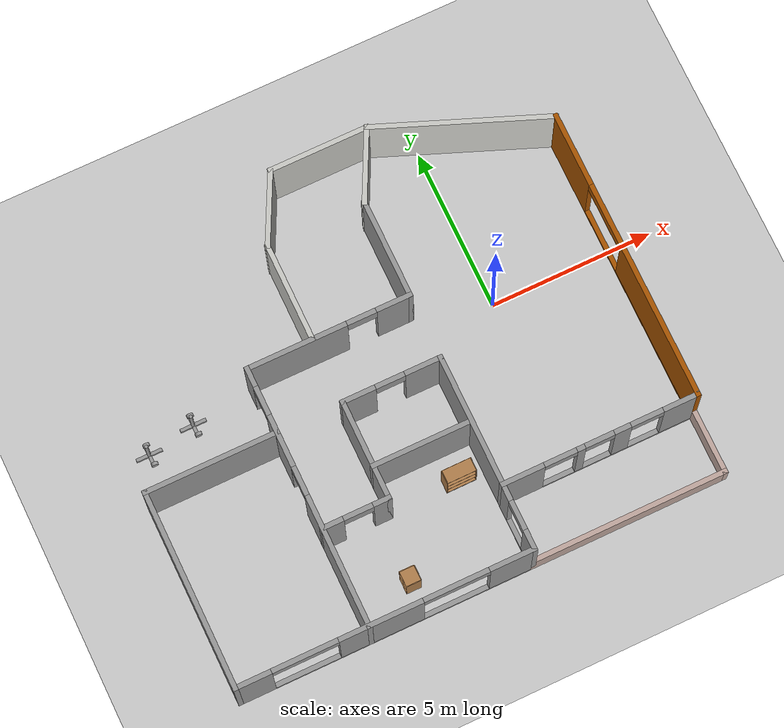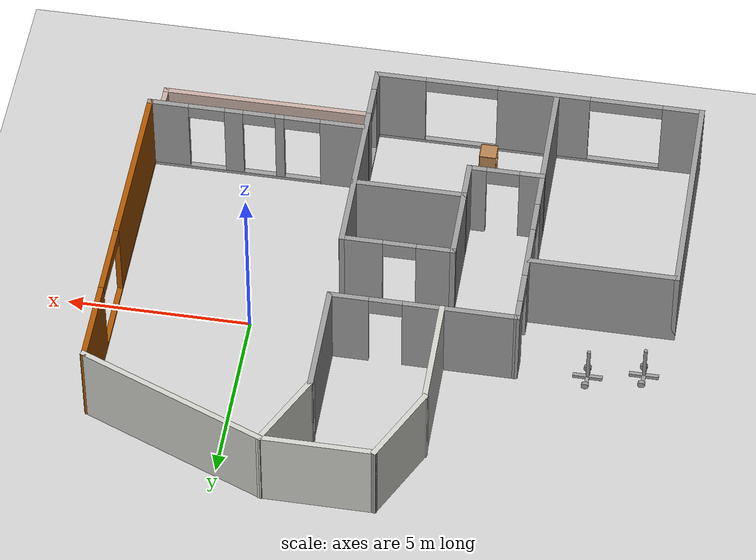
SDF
<sdf version="1.6">
 <world name="default">
  <plugin name="hello" filename="libhello_for_eimer.so"/>
  <light name="sun" type="directional">
   <pose>0 0 10 0 -0 0</pose>
   <diffuse>0.8 0.8 0.8 1</diffuse>
   <specular>0.1 0.1 0.1 1</specular>
   <attenuation>
    <range>1000</range>
    <constant>0.9</constant>
    <linear>0.01</linear>
    <quadratic>0.001</quadratic>
   </attenuation>
   <direction>-0.5 0.5 -1</direction>
  </light>
  <model name="ground_plane">
   <static>1</static>
   <link name="link">
    <collision name="collision">
     <geometry><plane><normal>0 0 1</normal><size>100 100</size></plane></geometry>
     <surface><friction><ode><mu>100</mu><mu2>50</mu2></ode></friction></surface>
    </collision>
    <visual name="visual">
     <cast_shadows>0</cast_shadows>
     <geometry><plane><normal>0 0 1</normal><size>100 100</size></plane></geometry>
     <material>
      <script><uri>file://media/materials/scripts/gazebo.material</uri><name>Gazebo/Grey</name></script>
     </material>
    </visual>
   </link>
  </model>
  <gravity>0 0 -9.8</gravity>
  <magnetic_field>6e-06 2.3e-05 -4.2e-05</magnetic_field>
  <atmosphere type="adiabatic"/>
  <physics name="default_physics" default="0" type="ode">
   <max_step_size>0.001</max_step_size>
   <real_time_factor>1</real_time_factor>
   <real_time_update_rate>1000</real_time_update_rate>
  </physics>
  <scene><ambient>0.4 0.4 0.4 1</ambient><background>0.7 0.7 0.7 1</background><shadows>1</shadows></scene>
  <spherical_coordinates>
   <surface_model>EARTH_WGS84</surface_model>
   <latitude_deg>0</latitude_deg>
   <longitude_deg>0</longitude_deg>
   <elevation>0</elevation>
   <heading_deg>0</heading_deg>
  </spherical_coordinates>
  <model name="Building">
   <pose>-3.80091 -0.843794 0 0 -0 0</pose>
   <link name="Wall_0">
    <collision name="Wall_0_Collision">
     <geometry><box><size>6.15 0.15 2.5</size></box></geometry>
     <pose>0 0 1.25 0 -0 0</pose>
    </collision>
    <visual name="Wall_0_Visual">
     <pose>0 0 1.25 0 -0 0</pose>
     <geometry><box><size>6.15 0.15 2.5</size></box></geometry>
     <material>
      <script><uri>file://media/materials/scripts/gazebo.material</uri><name>Gazebo/Grey</name></script>
      <ambient>1 1 1 1</ambient>
     </material>
     <meta><layer>0</layer></meta>
    </visual>
    <pose>-7.51124 -3.51281 0 0 -0 1.5708</pose>
   </link>
   <link name="Wall_12">
    <pose>-3.01125 -6.51281 0 0 -0 0</pose>
    <visual name="Wall_12_Visual_0">
     <pose>-3.99854 0 1.25 0 -0 0</pose>
     <geometry><box><size>1.15292 0.15 2.5</size></box></geometry>
     <material>
      <script><uri>file://media/materials/scripts/gazebo.material</uri><name>Gazebo/Grey</name></script>
      <ambient>1 1 1 1</ambient>
     </material>
     <meta><layer>0</layer></meta>
    </visual>
    <collision name="Wall_12_Collision_0">
     <geometry><box><size>1.15292 0.15 2.5</size></box></geometry>
     <pose>-3.99854 0 1.25 0 -0 0</pose>
    </collision>
    <visual name="Wall_12_Visual_1">
     <pose>0.57646 0 0.05 0 -0 0</pose>
     <geometry><box><size>7.99708 0.15 0.1</size></box></geometry>
     <material>
      <script><uri>file://media/materials/scripts/gazebo.material</uri><name>Gazebo/Grey</name></script>
      <ambient>1 1 1 1</ambient>
     </material>
     <meta><layer>0</layer></meta>
    </visual>
    <collision name="Wall_12_Collision_1">
     <geometry><box><size>7.99708 0.15 0.1</size></box></geometry>
     <pose>0.57646 0 0.05 0 -0 0</pose>
    </collision>
    <visual name="Wall_12_Visual_2">
     <pose>-0.143108 0 1.3 0 -0 0</pose>
     <geometry><box><size>2.55794 0.15 2.4</size></box></geometry>
     <material>
      <script><uri>file://media/materials/scripts/gazebo.material</uri><name>Gazebo/Grey</name></script>
      <ambient>1 1 1 1</ambient>
     </material>
     <meta><layer>0</layer></meta>
    </visual>
    <collision name="Wall_12_Collision_2">
     <geometry><box><size>2.55794 0.15 2.4</size></box></geometry>
     <pose>-0.143108 0 1.3 0 -0 0</pose>
    </collision>
    <visual name="Wall_12_Visual_3">
     <pose>3.85543 0 1.3 0 -0 0</pose>
     <geometry><box><size>1.43914 0.15 2.4</size></box></geometry>
     <material>
      <script><uri>file://media/materials/scripts/gazebo.material</uri><name>Gazebo/Grey</name></script>
      <ambient>1 1 1 1</ambient>
     </material>
     <meta><layer>0</layer></meta>
    </visual>
    <collision name="Wall_12_Collision_3">
     <geometry><box><size>1.43914 0.15 2.4</size></box></geometry>
     <pose>3.85543 0 1.3 0 -0 0</pose>
    </collision>
    <visual name="Wall_12_Visual_4">
     <pose>-2.42208 0 2.3 0 -0 0</pose>
     <geometry><box><size>2 0.15 0.4</size></box></geometry>
     <material>
      <script><uri>file://media/materials/scripts/gazebo.material</uri><name>Gazebo/Grey</name></script>
      <ambient>1 1 1 1</ambient>
     </material>
     <meta><layer>0</layer></meta>
    </visual>
    <collision name="Wall_12_Collision_4">
     <geometry><box><size>2 0.15 0.4</size></box></geometry>
     <pose>-2.42208 0 2.3 0 -0 0</pose>
    </collision>
    <visual name="Wall_12_Visual_5">
     <pose>2.13586 0 2.3 0 -0 0</pose>
     <geometry><box><size>2 0.15 0.4</size></box></geometry>
     <material>
      <script><uri>file://media/materials/scripts/gazebo.material</uri><name>Gazebo/Grey</name></script>
      <ambient>1 1 1 1</ambient>
     </material>
     <meta><layer>0</layer></meta>
    </visual>
    <collision name="Wall_12_Collision_5">
     <geometry><box><size>2 0.15 0.4</size></box></geometry>
     <pose>2.13586 0 2.3 0 -0 0</pose>
    </collision>
   </link>
   <link name="Wall_26">
    <pose>1.48876 -3.51281 0 0 0 -1.5708</pose>
    <visual name="Wall_26_Visual_0">
     <pose>-0.780552 0 1.25 0 -0 0</pose>
     <geometry><box><size>4.58889 0.15 2.5</size></box></geometry>
     <material>
      <script><uri>file://media/materials/scripts/gazebo.material</uri><name>Gazebo/Grey</name></script>
      <ambient>1 1 1 1</ambient>
     </material>
     <meta><layer>0</layer></meta>
    </visual>
    <collision name="Wall_26_Collision_0">
     <geometry><box><size>4.58889 0.15 2.5</size></box></geometry>
     <pose>-0.780552 0 1.25 0 -0 0</pose>
    </collision>
    <visual name="Wall_26_Visual_1">
     <pose>2.29445 0 0.05 0 -0 0</pose>
     <geometry><box><size>1.5611 0.15 0.1</size></box></geometry>
     <material>
      <script><uri>file://media/materials/scripts/gazebo.material</uri><name>Gazebo/Grey</name></script>
      <ambient>1 1 1 1</ambient>
     </material>
     <meta><layer>0</layer></meta>
    </visual>
    <collision name="Wall_26_Collision_1">
     <geometry><box><size>1.5611 0.15 0.1</size></box></geometry>
     <pose>2.29445 0 0.05 0 -0 0</pose>
    </collision>
    <visual name="Wall_26_Visual_2">
     <pose>2.74445 0 1.3 0 -0 0</pose>
     <geometry><box><size>0.661105 0.15 2.4</size></box></geometry>
     <material>
      <script><uri>file://media/materials/scripts/gazebo.material</uri><name>Gazebo/Grey</name></script>
      <ambient>1 1 1 1</ambient>
     </material>
     <meta><layer>0</layer></meta>
    </visual>
    <collision name="Wall_26_Collision_2">
     <geometry><box><size>0.661105 0.15 2.4</size></box></geometry>
     <pose>2.74445 0 1.3 0 -0 0</pose>
    </collision>
    <visual name="Wall_26_Visual_3">
     <pose>1.96389 0 2.3 0 -0 0</pose>
     <geometry><box><size>0.9 0.15 0.4</size></box></geometry>
     <material>
      <script><uri>file://media/materials/scripts/gazebo.material</uri><name>Gazebo/Grey</name></script>
      <ambient>1 1 1 1</ambient>
     </material>
     <meta><layer>0</layer></meta>
    </visual>
    <collision name="Wall_26_Collision_3">
     <geometry><box><size>0.9 0.15 0.4</size></box></geometry>
     <pose>1.96389 0 2.3 0 -0 0</pose>
    </collision>
   </link>
   <link name="Wall_28">
    <collision name="Wall_28_Collision">
     <geometry><box><size>3.15 0.15 2.5</size></box></geometry>
     <pose>0 0 1.25 0 -0 0</pose>
    </collision>
    <visual name="Wall_28_Visual">
     <pose>0 0 1.25 0 -0 0</pose>
     <geometry><box><size>3.15 0.15 2.5</size></box></geometry>
     <material>
      <script><uri>file://media/materials/scripts/gazebo.material</uri><name>Gazebo/Grey</name></script>
      <ambient>1 1 1 1</ambient>
     </material>
     <meta><layer>0</layer></meta>
    </visual>
    <pose>1.48876 2.98719 0 0 -0 1.5708</pose>
   </link>
   <link name="Wall_30">
    <collision name="Wall_30_Collision">
     <geometry><box><size>2.38607 0.15 2.5</size></box></geometry>
     <pose>0 0 1.25 0 -0 0</pose>
    </collision>
    <visual name="Wall_30_Visual">
     <pose>0 0 1.25 0 -0 0</pose>
     <geometry><box><size>2.38607 0.15 2.5</size></box></geometry>
     <material>
      <script><uri>file://media/materials/scripts/gazebo.material</uri><name>Gazebo/CeilingTiled</name></script>
      <ambient>1 1 1 1</ambient>
     </material>
     <meta><layer>0</layer></meta>
    </visual>
    <pose>1.98876 5.48719 0 0 -0 1.10715</pose>
   </link>
   <link name="Wall_32">
    <pose>7.48876 -0.012811 0 0 0 -1.5708</pose>
    <visual name="Wall_32_Visual_0">
     <pose>-3.40699 0 1.25 0 -0 0</pose>
     <geometry><box><size>2.33601 0.15 2.5</size></box></geometry>
     <material>
      <script><uri>file://media/materials/scripts/gazebo.material</uri><name>Gazebo/Grey</name></script>
      <ambient>0.666667 0.333333 0 1</ambient>
     </material>
     <meta><layer>0</layer></meta>
    </visual>
    <collision name="Wall_32_Collision_0">
     <geometry><box><size>2.33601 0.15 2.5</size></box></geometry>
     <pose>-3.40699 0 1.25 0 -0 0</pose>
    </collision>
    <visual name="Wall_32_Visual_1">
     <pose>1.16801 0 0.05 0 -0 0</pose>
     <geometry><box><size>6.81399 0.15 0.1</size></box></geometry>
     <material>
      <script><uri>file://media/materials/scripts/gazebo.material</uri><name>Gazebo/Grey</name></script>
      <ambient>0.666667 0.333333 0 1</ambient>
     </material>
     <meta><layer>0</layer></meta>
    </visual>
    <collision name="Wall_32_Collision_1">
     <geometry><box><size>6.81399 0.15 0.1</size></box></geometry>
     <pose>1.16801 0 0.05 0 -0 0</pose>
    </collision>
    <visual name="Wall_32_Visual_2">
     <pose>2.16801 0 1.3 0 -0 0</pose>
     <geometry><box><size>4.81399 0.15 2.4</size></box></geometry>
     <material>
      <script><uri>file://media/materials/scripts/gazebo.material</uri><name>Gazebo/Grey</name></script>
      <ambient>0.666667 0.333333 0 1</ambient>
     </material>
     <meta><layer>0</layer></meta>
    </visual>
    <collision name="Wall_32_Collision_2">
     <geometry><box><size>4.81399 0.15 2.4</size></box></geometry>
     <pose>2.16801 0 1.3 0 -0 0</pose>
    </collision>
    <visual name="Wall_32_Visual_3">
     <pose>-1.23899 0 2.3 0 -0 0</pose>
     <geometry><box><size>2 0.15 0.4</size></box></geometry>
     <material>
      <script><uri>file://media/materials/scripts/gazebo.material</uri><name>Gazebo/Grey</name></script>
      <ambient>0.666667 0.333333 0 1</ambient>
     </material>
     <meta><layer>0</layer></meta>
    </visual>
    <collision name="Wall_32_Collision_3">
     <geometry><box><size>2 0.15 0.4</size></box></geometry>
     <pose>-1.23899 0 2.3 0 -0 0</pose>
    </collision>
   </link>
   <link name="Wall_34">
    <collision name="Wall_34_Collision">
     <geometry><box><size>6.15 0.15 0.8</size></box></geometry>
     <pose>0 0 0.4 0 -0 0</pose>
    </collision>
    <visual name="Wall_34_Visual">
     <pose>0 0 0.4 0 -0 0</pose>
     <geometry><box><size>6.15 0.15 0.8</size></box></geometry>
     <material>
      <script><uri>file://media/materials/scripts/gazebo.material</uri><name>Gazebo/Grey</name></script>
      <ambient>0.760784 0.662745 0.627451 1</ambient>
     </material>
     <meta><layer>0</layer></meta>
    </visual>
    <pose>4.48876 -6.51281 0 0 -0 0</pose>
   </link>
   <link name="Wall_36">
    <pose>4.48876 -4.51281 0 0 -0 0</pose>
    <visual name="Wall_36_Visual_0">
     <pose>-2.40473 0 1.25 0 -0 0</pose>
     <geometry><box><size>1.34055 0.15 2.5</size></box></geometry>
     <material>
      <script><uri>file://media/materials/scripts/gazebo.material</uri><name>Gazebo/Grey</name></script>
      <ambient>1 1 1 1</ambient>
     </material>
     <meta><layer>0</layer></meta>
    </visual>
    <collision name="Wall_36_Collision_0">
     <geometry><box><size>1.34055 0.15 2.5</size></box></geometry>
     <pose>-2.40473 0 1.25 0 -0 0</pose>
    </collision>
    <visual name="Wall_36_Visual_1">
     <pose>0.670272 0 0.05 0 -0 0</pose>
     <geometry><box><size>4.80945 0.15 0.1</size></box></geometry>
     <material>
      <script><uri>file://media/materials/scripts/gazebo.material</uri><name>Gazebo/Grey</name></script>
      <ambient>1 1 1 1</ambient>
     </material>
     <meta><layer>0</layer></meta>
    </visual>
    <collision name="Wall_36_Collision_1">
     <geometry><box><size>4.80945 0.15 0.1</size></box></geometry>
     <pose>0.670272 0 0.05 0 -0 0</pose>
    </collision>
    <visual name="Wall_36_Visual_2">
     <pose>-0.610532 0 1.3 0 -0 0</pose>
     <geometry><box><size>0.247846 0.15 2.4</size></box></geometry>
     <material>
      <script><uri>file://media/materials/scripts/gazebo.material</uri><name>Gazebo/Grey</name></script>
      <ambient>1 1 1 1</ambient>
     </material>
     <meta><layer>0</layer></meta>
    </visual>
    <collision name="Wall_36_Collision_2">
     <geometry><box><size>0.247846 0.15 2.4</size></box></geometry>
     <pose>-0.610532 0 1.3 0 -0 0</pose>
    </collision>
    <visual name="Wall_36_Visual_3">
     <pose>0.670143 0 1.3 0 -0 0</pose>
     <geometry><box><size>0.513504 0.15 2.4</size></box></geometry>
     <material>
      <script><uri>file://media/materials/scripts/gazebo.material</uri><name>Gazebo/Grey</name></script>
      <ambient>1 1 1 1</ambient>
     </material>
     <meta><layer>0</layer></meta>
    </visual>
    <collision name="Wall_36_Collision_3">
     <geometry><box><size>0.513504 0.15 2.4</size></box></geometry>
     <pose>0.670143 0 1.3 0 -0 0</pose>
    </collision>
    <visual name="Wall_36_Visual_4">
     <pose>2.50095 0 1.3 0 -0 0</pose>
     <geometry><box><size>1.1481 0.15 2.4</size></box></geometry>
     <material>
      <script><uri>file://media/materials/scripts/gazebo.material</uri><name>Gazebo/Grey</name></script>
      <ambient>1 1 1 1</ambient>
     </material>
     <meta><layer>0</layer></meta>
    </visual>
    <collision name="Wall_36_Collision_4">
     <geometry><box><size>1.1481 0.15 2.4</size></box></geometry>
     <pose>2.50095 0 1.3 0 -0 0</pose>
    </collision>
    <visual name="Wall_36_Visual_5">
     <pose>-1.23446 0 2.3 0 -0 0</pose>
     <geometry><box><size>1 0.15 0.4</size></box></geometry>
     <material>
      <script><uri>file://media/materials/scripts/gazebo.material</uri><name>Gazebo/Grey</name></script>
      <ambient>1 1 1 1</ambient>
     </material>
     <meta><layer>0</layer></meta>
    </visual>
    <collision name="Wall_36_Collision_5">
     <geometry><box><size>1 0.15 0.4</size></box></geometry>
     <pose>-1.23446 0 2.3 0 -0 0</pose>
    </collision>
    <visual name="Wall_36_Visual_6">
     <pose>-0.036609 0 2.3 0 -0 0</pose>
     <geometry><box><size>0.9 0.15 0.4</size></box></geometry>
     <material>
      <script><uri>file://media/materials/scripts/gazebo.material</uri><name>Gazebo/Grey</name></script>
      <ambient>1 1 1 1</ambient>
     </material>
     <meta><layer>0</layer></meta>
    </visual>
    <collision name="Wall_36_Collision_6">
     <geometry><box><size>0.9 0.15 0.4</size></box></geometry>
     <pose>-0.036609 0 2.3 0 -0 0</pose>
    </collision>
    <visual name="Wall_36_Visual_7">
     <pose>1.4269 0 2.3 0 -0 0</pose>
     <geometry><box><size>1 0.15 0.4</size></box></geometry>
     <material>
      <script><uri>file://media/materials/scripts/gazebo.material</uri><name>Gazebo/Grey</name></script>
      <ambient>1 1 1 1</ambient>
     </material>
     <meta><layer>0</layer></meta>
    </visual>
    <collision name="Wall_36_Collision_7">
     <geometry><box><size>1 0.15 0.4</size></box></geometry>
     <pose>1.4269 0 2.3 0 -0 0</pose>
    </collision>
   </link>
   <link name="Wall_38">
    <pose>-1.01124 1.48719 0 0 -0 0</pose>
    <visual name="Wall_38_Visual_0">
     <pose>-1.0103 0 1.25 0 -0 0</pose>
     <geometry><box><size>3.1294 0.15 2.5</size></box></geometry>
     <material>
      <script><uri>file://media/materials/scripts/gazebo.material</uri><name>Gazebo/Grey</name></script>
      <ambient>1 1 1 1</ambient>
     </material>
     <meta><layer>0</layer></meta>
    </visual>
    <collision name="Wall_38_Collision_0">
     <geometry><box><size>3.1294 0.15 2.5</size></box></geometry>
     <pose>-1.0103 0 1.25 0 -0 0</pose>
    </collision>
    <visual name="Wall_38_Visual_1">
     <pose>2.0147 0 1.25 0 -0 0</pose>
     <geometry><box><size>1.1206 0.15 2.5</size></box></geometry>
     <material>
      <script><uri>file://media/materials/scripts/gazebo.material</uri><name>Gazebo/Grey</name></script>
      <ambient>1 1 1 1</ambient>
     </material>
     <meta><layer>0</layer></meta>
    </visual>
    <collision name="Wall_38_Collision_1">
     <geometry><box><size>1.1206 0.15 2.5</size></box></geometry>
     <pose>2.0147 0 1.25 0 -0 0</pose>
    </collision>
    <visual name="Wall_38_Visual_2">
     <pose>1.0044 0 2.25 0 -0 0</pose>
     <geometry><box><size>0.9 0.15 0.5</size></box></geometry>
     <material>
      <script><uri>file://media/materials/scripts/gazebo.material</uri><name>Gazebo/Grey</name></script>
      <ambient>1 1 1 1</ambient>
     </material>
     <meta><layer>0</layer></meta>
    </visual>
    <collision name="Wall_38_Collision_2">
     <geometry><box><size>0.9 0.15 0.5</size></box></geometry>
     <pose>1.0044 0 2.25 0 -0 0</pose>
    </collision>
   </link>
   <link name="Wall_4">
    <pose>-3.51125 -2.51281 0 0 -0 1.5708</pose>
    <visual name="Wall_4_Visual_0">
     <pose>-2.02622 0 1.25 0 -0 0</pose>
     <geometry><box><size>4.09757 0.15 2.5</size></box></geometry>
     <material>
      <script><uri>file://media/materials/scripts/gazebo.material</uri><name>Gazebo/Grey</name></script>
      <ambient>1 1 1 1</ambient>
     </material>
     <meta><layer>0</layer></meta>
    </visual>
    <collision name="Wall_4_Collision_0">
     <geometry><box><size>4.09757 0.15 2.5</size></box></geometry>
     <pose>-2.02622 0 1.25 0 -0 0</pose>
    </collision>
    <visual name="Wall_4_Visual_1">
     <pose>1.72967 0 1.25 0 -0 0</pose>
     <geometry><box><size>1.6142 0.15 2.5</size></box></geometry>
     <material>
      <script><uri>file://media/materials/scripts/gazebo.material</uri><name>Gazebo/Grey</name></script>
      <ambient>1 1 1 1</ambient>
     </material>
     <meta><layer>0</layer></meta>
    </visual>
    <collision name="Wall_4_Collision_1">
     <geometry><box><size>1.6142 0.15 2.5</size></box></geometry>
     <pose>1.72967 0 1.25 0 -0 0</pose>
    </collision>
    <visual name="Wall_4_Visual_2">
     <pose>3.75588 0 1.25 0 -0 0</pose>
     <geometry><box><size>0.638237 0.15 2.5</size></box></geometry>
     <material>
      <script><uri>file://media/materials/scripts/gazebo.material</uri><name>Gazebo/Grey</name></script>
      <ambient>1 1 1 1</ambient>
     </material>
     <meta><layer>0</layer></meta>
    </visual>
    <collision name="Wall_4_Collision_2">
     <geometry><box><size>0.638237 0.15 2.5</size></box></geometry>
     <pose>3.75588 0 1.25 0 -0 0</pose>
    </collision>
    <visual name="Wall_4_Visual_3">
     <pose>0.472567 0 2.25 0 -0 0</pose>
     <geometry><box><size>0.9 0.15 0.5</size></box></geometry>
     <material>
      <script><uri>file://media/materials/scripts/gazebo.material</uri><name>Gazebo/Grey</name></script>
      <ambient>1 1 1 1</ambient>
     </material>
     <meta><layer>0</layer></meta>
    </visual>
    <collision name="Wall_4_Collision_3">
     <geometry><box><size>0.9 0.15 0.5</size></box></geometry>
     <pose>0.472567 0 2.25 0 -0 0</pose>
    </collision>
    <visual name="Wall_4_Visual_4">
     <pose>2.98676 0 2.25 0 -0 0</pose>
     <geometry><box><size>0.9 0.15 0.5</size></box></geometry>
     <material>
      <script><uri>file://media/materials/scripts/gazebo.material</uri><name>Gazebo/Grey</name></script>
      <ambient>1 1 1 1</ambient>
     </material>
     <meta><layer>0</layer></meta>
    </visual>
    <collision name="Wall_4_Collision_4">
     <geometry><box><size>0.9 0.15 0.5</size></box></geometry>
     <pose>2.98676 0 2.25 0 -0 0</pose>
    </collision>
   </link>
   <link name="Wall_40">
    <pose>-0.011245 -0.512811 0 0 -0 0</pose>
    <visual name="Wall_40_Visual_0">
     <pose>-1.04047 0 1.25 0 -0 0</pose>
     <geometry><box><size>1.06906 0.15 2.5</size></box></geometry>
     <material>
      <script><uri>file://media/materials/scripts/gazebo.material</uri><name>Gazebo/Grey</name></script>
      <ambient>1 1 1 1</ambient>
     </material>
     <meta><layer>0</layer></meta>
    </visual>
    <collision name="Wall_40_Collision_0">
     <geometry><box><size>1.06906 0.15 2.5</size></box></geometry>
     <pose>-1.04047 0 1.25 0 -0 0</pose>
    </collision>
    <visual name="Wall_40_Visual_1">
     <pose>0.984528 0 1.25 0 -0 0</pose>
     <geometry><box><size>1.18094 0.15 2.5</size></box></geometry>
     <material>
      <script><uri>file://media/materials/scripts/gazebo.material</uri><name>Gazebo/Grey</name></script>
      <ambient>1 1 1 1</ambient>
     </material>
     <meta><layer>0</layer></meta>
    </visual>
    <collision name="Wall_40_Collision_1">
     <geometry><box><size>1.18094 0.15 2.5</size></box></geometry>
     <pose>0.984528 0 1.25 0 -0 0</pose>
    </collision>
    <visual name="Wall_40_Visual_2">
     <pose>-0.055943 0 2.25 0 -0 0</pose>
     <geometry><box><size>0.9 0.15 0.5</size></box></geometry>
     <material>
      <script><uri>file://media/materials/scripts/gazebo.material</uri><name>Gazebo/Grey</name></script>
      <ambient>1 1 1 1</ambient>
     </material>
     <meta><layer>0</layer></meta>
    </visual>
    <collision name="Wall_40_Collision_2">
     <geometry><box><size>0.9 0.15 0.5</size></box></geometry>
     <pose>-0.055943 0 2.25 0 -0 0</pose>
    </collision>
   </link>
   <link name="Wall_42">
    <collision name="Wall_42_Collision">
     <geometry><box><size>3.15 0.15 2.5</size></box></geometry>
     <pose>0 0 1.25 0 -0 0</pose>
    </collision>
    <visual name="Wall_42_Visual">
     <pose>0 0 1.25 0 -0 0</pose>
     <geometry><box><size>3.15 0.15 2.5</size></box></geometry>
     <material>
      <script><uri>file://media/materials/scripts/gazebo.material</uri><name>Gazebo/Grey</name></script>
      <ambient>1 1 1 1</ambient>
     </material>
     <meta><layer>0</layer></meta>
    </visual>
    <pose>-0.011245 -2.51281 0 0 -0 0</pose>
   </link>
   <link name="Wall_44">
    <collision name="Wall_44_Collision">
     <geometry><box><size>3.15 0.15 2.5</size></box></geometry>
     <pose>0 0 1.25 0 -0 0</pose>
    </collision>
    <visual name="Wall_44_Visual">
     <pose>0 0 1.25 0 -0 0</pose>
     <geometry><box><size>3.15 0.15 2.5</size></box></geometry>
     <material>
      <script><uri>file://media/materials/scripts/gazebo.material</uri><name>Gazebo/Grey</name></script>
      <ambient>1 1 1 1</ambient>
     </material>
     <meta><layer>0</layer></meta>
    </visual>
    <pose>-1.51124 -2.01281 0 0 0 -1.5708</pose>
   </link>
   <link name="Wall_46">
    <pose>-2.51125 -3.51281 0 0 -0 0</pose>
    <visual name="Wall_46_Visual_0">
     <pose>-0.727172 0 1.25 0 -0 0</pose>
     <geometry><box><size>0.695655 0.15 2.5</size></box></geometry>
     <material>
      <script><uri>file://media/materials/scripts/gazebo.material</uri><name>Gazebo/Grey</name></script>
      <ambient>1 1 1 1</ambient>
     </material>
     <meta><layer>0</layer></meta>
    </visual>
    <collision name="Wall_46_Collision_0">
     <geometry><box><size>0.695655 0.15 2.5</size></box></geometry>
     <pose>-0.727172 0 1.25 0 -0 0</pose>
    </collision>
    <visual name="Wall_46_Visual_1">
     <pose>0.797828 0 1.25 0 -0 0</pose>
     <geometry><box><size>0.554345 0.15 2.5</size></box></geometry>
     <material>
      <script><uri>file://media/materials/scripts/gazebo.material</uri><name>Gazebo/Grey</name></script>
      <ambient>1 1 1 1</ambient>
     </material>
     <meta><layer>0</layer></meta>
    </visual>
    <collision name="Wall_46_Collision_1">
     <geometry><box><size>0.554345 0.15 2.5</size></box></geometry>
     <pose>0.797828 0 1.25 0 -0 0</pose>
    </collision>
    <visual name="Wall_46_Visual_2">
     <pose>0.070655 0 2.25 0 -0 0</pose>
     <geometry><box><size>0.9 0.15 0.5</size></box></geometry>
     <material>
      <script><uri>file://media/materials/scripts/gazebo.material</uri><name>Gazebo/Grey</name></script>
      <ambient>1 1 1 1</ambient>
     </material>
     <meta><layer>0</layer></meta>
    </visual>
    <collision name="Wall_46_Collision_2">
     <geometry><box><size>0.9 0.15 0.5</size></box></geometry>
     <pose>0.070655 0 2.25 0 -0 0</pose>
    </collision>
   </link>
   <link name="Wall_48">
    <collision name="Wall_48_Collision">
     <geometry><box><size>4.15 0.15 2.5</size></box></geometry>
     <pose>0 0 1.25 0 -0 0</pose>
    </collision>
    <visual name="Wall_48_Visual">
     <pose>0 0 1.25 0 -0 0</pose>
     <geometry><box><size>4.15 0.15 2.5</size></box></geometry>
     <material>
      <script><uri>file://media/materials/scripts/gazebo.material</uri><name>Gazebo/Grey</name></script>
      <ambient>1 1 1 1</ambient>
     </material>
     <meta><layer>0</layer></meta>
    </visual>
    <pose>-5.51124 -0.512811 0 0 -0 0</pose>
   </link>
   <link name="Wall_50">
    <collision name="Wall_50_Collision">
     <geometry><box><size>3.15 0.15 2.5</size></box></geometry>
     <pose>0 0 1.25 0 -0 0</pose>
    </collision>
    <visual name="Wall_50_Visual">
     <pose>0 0 1.25 0 -0 0</pose>
     <geometry><box><size>3.15 0.15 2.5</size></box></geometry>
     <material>
      <script><uri>file://media/materials/scripts/gazebo.material</uri><name>Gazebo/CeilingTiled</name></script>
      <ambient>1 1 1 1</ambient>
     </material>
     <meta><layer>0</layer></meta>
    </visual>
    <pose>0.988755 6.48719 0 0 -0 0</pose>
   </link>
   <link name="Wall_52">
    <collision name="Wall_52_Collision">
     <geometry><box><size>5.53517 0.15 2.5</size></box></geometry>
     <pose>0 0 1.25 0 -0 0</pose>
    </collision>
    <visual name="Wall_52_Visual">
     <pose>0 0 1.25 0 -0 0</pose>
     <geometry><box><size>5.53517 0.15 2.5</size></box></geometry>
     <material>
      <script><uri>file://media/materials/scripts/gazebo.material</uri><name>Gazebo/CeilingTiled</name></script>
      <ambient>1 1 1 1</ambient>
     </material>
     <meta><layer>0</layer></meta>
    </visual>
    <pose>4.98876 5.48719 0 0 0 -0.380506</pose>
   </link>
   <link name="Wall_54">
    <collision name="Wall_54_Collision">
     <geometry><box><size>2.15 0.15 0.8</size></box></geometry>
     <pose>0 0 0.4 0 -0 0</pose>
    </collision>
    <visual name="Wall_54_Visual">
     <pose>0 0 0.4 0 -0 0</pose>
     <geometry><box><size>2.15 0.15 0.8</size></box></geometry>
     <material>
      <script><uri>file://media/materials/scripts/gazebo.material</uri><name>Gazebo/Grey</name></script>
      <ambient>0.760784 0.662745 0.627451 1</ambient>
     </material>
     <meta><layer>0</layer></meta>
    </visual>
    <pose>7.48876 -5.51281 0 0 0 -1.5708</pose>
   </link>
   <link name="Wall_6">
    <collision name="Wall_6_Collision">
     <geometry><box><size>2.38607 0.15 2.5</size></box></geometry>
     <pose>0 0 1.25 0 -0 0</pose>
    </collision>
    <visual name="Wall_6_Visual">
     <pose>0 0 1.25 0 -0 0</pose>
     <geometry><box><size>2.38607 0.15 2.5</size></box></geometry>
     <material>
      <script><uri>file://media/materials/scripts/gazebo.material</uri><name>Gazebo/CeilingTiled</name></script>
      <ambient>1 1 1 1</ambient>
     </material>
     <meta><layer>0</layer></meta>
    </visual>
    <pose>-1.01124 5.48719 0 0 -0 1.10715</pose>
   </link>
   <link name="Wall_7">
    <collision name="Wall_7_Collision">
     <geometry><box><size>0.15 0.15 2.5</size></box></geometry>
     <pose>0 0 1.25 0 -0 0</pose>
    </collision>
    <visual name="Wall_7_Visual">
     <pose>0 0 1.25 0 -0 0</pose>
     <geometry><box><size>0.15 0.15 2.5</size></box></geometry>
     <material>
      <script><uri>file://media/materials/scripts/gazebo.material</uri><name>Gazebo/Grey</name></script>
      <ambient>1 1 1 1</ambient>
     </material>
     <meta><layer>0</layer></meta>
    </visual>
    <pose>-0.511245 6.48719 0 0 -0 0</pose>
   </link>
   <link name="Wall_9">
    <collision name="Wall_9_Collision">
     <geometry><box><size>3.15 0.15 2.5</size></box></geometry>
     <pose>0 0 1.25 0 -0 0</pose>
    </collision>
    <visual name="Wall_9_Visual">
     <pose>0 0 1.25 0 -0 0</pose>
     <geometry><box><size>3.15 0.15 2.5</size></box></geometry>
     <material>
      <script><uri>file://media/materials/scripts/gazebo.material</uri><name>Gazebo/CeilingTiled</name></script>
      <ambient>1 1 1 1</ambient>
     </material>
     <meta><layer>0</layer></meta>
    </visual>
    <pose>-1.51124 2.98719 0 0 0 -1.5708</pose>
   </link>
   <static>1</static>
  </model>
  <model name="EimerRobot">
   <link name="link_0_clone">
    <pose>2.5834 -4.84657 0.119047 0 -0 0</pose>
    <inertial>
     <mass>1</mass>
     <inertia>
      <ixx>0.166667</ixx>
      <ixy>0</ixy>
      <ixz>0</ixz>
      <iyy>0.166667</iyy>
      <iyz>0</iyz>
      <izz>0.166667</izz>
     </inertia>
    </inertial>
    <visual name="visual">
     <geometry><box><size>0.1 0.5 0.1</size></box></geometry>
     <material>
      <lighting>1</lighting>
      <script><uri>file://media/materials/scripts/gazebo.material</uri><name>Gazebo/Grey</name></script>
      <shader type="pixel"><normal_map>__default__</normal_map></shader>
      <ambient>0.3 0.3 0.3 1</ambient>
      <diffuse>0.7 0.7 0.7 1</diffuse>
      <specular>0.01 0.01 0.01 1</specular>
      <emissive>0 0 0 1</emissive>
     </material>
    </visual>
    <collision name="collision">
     <geometry><box><size>0.1 0.5 0.1</size></box></geometry>
     <surface>
      <friction>
       <ode><mu>1</mu><mu2>1</mu2><fdir1>0 0 0</fdir1><slip1>0</slip1><slip2>0</slip2></ode>
       <torsional>
        <coefficient>1</coefficient>
        <patch_radius>0</patch_radius>
        <surface_radius>0</surface_radius>
        <use_patch_radius>1</use_patch_radius>
        <ode><slip>0</slip></ode>
       </torsional>
      </friction>
      <bounce><restitution_coefficient>0</restitution_coefficient><threshold>1e+06</threshold></bounce>
      <contact>
       <collide_without_contact>0</collide_without_contact>
       <collide_without_contact_bitmask>1</collide_without_contact_bitmask>
       <collide_bitmask>1</collide_bitmask>
       <ode>
        <soft_cfm>0</soft_cfm>
        <soft_erp>0.2</soft_erp>
        <kp>1e+13</kp>
        <kd>1</kd>
        <max_vel>0.01</max_vel>
        <min_depth>0</min_depth>
       </ode>
       <bullet>
        <split_impulse>1</split_impulse>
        <split_impulse_penetration_threshold>-0.01</split_impulse_penetration_threshold>
        <soft_cfm>0</soft_cfm>
        <soft_erp>0.2</soft_erp>
        <kp>1e+13</kp>
        <kd>1</kd>
       </bullet>
      </contact>
     </surface>
    </collision>
   </link>
   <link name="link_0_clone_clone">
    <pose>2.58152 -4.846 0.119047 0 -0 1.5707</pose>
    <inertial>
     <mass>1</mass>
     <inertia>
      <ixx>0.166667</ixx>
      <ixy>0</ixy>
      <ixz>0</ixz>
      <iyy>0.166667</iyy>
      <iyz>0</iyz>
      <izz>0.166667</izz>
     </inertia>
    </inertial>
    <visual name="visual">
     <geometry><box><size>0.1 0.8 0.1</size></box></geometry>
     <material>
      <lighting>1</lighting>
      <script><uri>file://media/materials/scripts/gazebo.material</uri><name>Gazebo/Grey</name></script>
      <shader type="pixel"><normal_map>__default__</normal_map></shader>
      <ambient>0.3 0.3 0.3 1</ambient>
      <diffuse>0.7 0.7 0.7 1</diffuse>
      <specular>0.01 0.01 0.01 1</specular>
      <emissive>0 0 0 1</emissive>
     </material>
    </visual>
    <collision name="collision">
     <geometry><box><size>0.1 0.8 0.1</size></box></geometry>
     <surface>
      <friction>
       <ode><mu>1</mu><mu2>1</mu2><fdir1>0 0 0</fdir1><slip1>0</slip1><slip2>0</slip2></ode>
       <torsional>
        <coefficient>1</coefficient>
        <patch_radius>0</patch_radius>
        <surface_radius>0</surface_radius>
        <use_patch_radius>1</use_patch_radius>
        <ode><slip>0</slip></ode>
       </torsional>
      </friction>
      <bounce><restitution_coefficient>0</restitution_coefficient><threshold>1e+06</threshold></bounce>
      <contact>
       <collide_without_contact>0</collide_without_contact>
       <collide_without_contact_bitmask>1</collide_without_contact_bitmask>
       <collide_bitmask>1</collide_bitmask>
       <ode>
        <soft_cfm>0</soft_cfm>
        <soft_erp>0.2</soft_erp>
        <kp>1e+13</kp>
        <kd>1</kd>
        <max_vel>0.01</max_vel>
        <min_depth>0</min_depth>
       </ode>
       <bullet>
        <split_impulse>1</split_impulse>
        <split_impulse_penetration_threshold>-0.01</split_impulse_penetration_threshold>
        <soft_cfm>0</soft_cfm>
        <soft_erp>0.2</soft_erp>
        <kp>1e+13</kp>
        <kd>1</kd>
       </bullet>
      </contact>
     </surface>
    </collision>
   </link>
   <link name="link_1_clone">
    <pose>2.61519 -4.54652 0.119046 1.5707 -0 0</pose>
    <inertial>
     <mass>1</mass>
     <inertia><ixx>0.145833</ixx><ixy>0</ixy><ixz>0</ixz><iyy>0.145833</iyy><iyz>0</iyz><izz>0.125</izz></inertia>
    </inertial>
    <visual name="visual">
     <geometry><cylinder><radius>0.1</radius><length>0.1</length></cylinder></geometry>
     <material>
      <lighting>1</lighting>
      <script><uri>file://media/materials/scripts/gazebo.material</uri><name>Gazebo/Grey</name></script>
      <shader type="pixel"><normal_map>__default__</normal_map></shader>
      <ambient>0.3 0.3 0.3 1</ambient>
      <diffuse>0.7 0.7 0.7 1</diffuse>
      <specular>0.01 0.01 0.01 1</specular>
      <emissive>0 0 0 1</emissive>
     </material>
    </visual>
    <collision name="collision">
     <geometry><cylinder><radius>0.1</radius><length>0.1</length></cylinder></geometry>
     <surface>
      <friction>
       <ode><mu>1</mu><mu2>1</mu2><fdir1>0 0 0</fdir1><slip1>0</slip1><slip2>0</slip2></ode>
       <torsional>
        <coefficient>1</coefficient>
        <patch_radius>0</patch_radius>
        <surface_radius>0</surface_radius>
        <use_patch_radius>1</use_patch_radius>
        <ode><slip>0</slip></ode>
       </torsional>
      </friction>
      <bounce><restitution_coefficient>0</restitution_coefficient><threshold>1e+06</threshold></bounce>
      <contact>
       <collide_without_contact>0</collide_without_contact>
       <collide_without_contact_bitmask>1</collide_without_contact_bitmask>
       <collide_bitmask>1</collide_bitmask>
       <ode>
        <soft_cfm>0</soft_cfm>
        <soft_erp>0.2</soft_erp>
        <kp>1e+13</kp>
        <kd>1</kd>
        <max_vel>0.01</max_vel>
        <min_depth>0</min_depth>
       </ode>
       <bullet>
        <split_impulse>1</split_impulse>
        <split_impulse_penetration_threshold>-0.01</split_impulse_penetration_threshold>
        <soft_cfm>0</soft_cfm>
        <soft_erp>0.2</soft_erp>
        <kp>1e+13</kp>
        <kd>1</kd>
       </bullet>
      </contact>
     </surface>
    </collision>
   </link>
   <link name="link_1_clone_clone">
    <pose>2.61534 -5.14663 0.119047 1.5707 -0 0</pose>
    <inertial>
     <mass>1</mass>
     <inertia><ixx>0.145833</ixx><ixy>0</ixy><ixz>0</ixz><iyy>0.145833</iyy><iyz>0</iyz><izz>0.125</izz></inertia>
    </inertial>
    <visual name="visual">
     <geometry><cylinder><radius>0.1</radius><length>0.1</length></cylinder></geometry>
     <material>
      <lighting>1</lighting>
      <script><uri>file://media/materials/scripts/gazebo.material</uri><name>Gazebo/Grey</name></script>
      <shader type="pixel"><normal_map>__default__</normal_map></shader>
      <ambient>0.3 0.3 0.3 1</ambient>
      <diffuse>0.7 0.7 0.7 1</diffuse>
      <specular>0.01 0.01 0.01 1</specular>
      <emissive>0 0 0 1</emissive>
     </material>
    </visual>
    <collision name="collision">
     <geometry><cylinder><radius>0.1</radius><length>0.1</length></cylinder></geometry>
     <surface>
      <friction>
       <ode><mu>1</mu><mu2>1</mu2><fdir1>0 0 0</fdir1><slip1>0</slip1><slip2>0</slip2></ode>
       <torsional>
        <coefficient>1</coefficient>
        <patch_radius>0</patch_radius>
        <surface_radius>0</surface_radius>
        <use_patch_radius>1</use_patch_radius>
        <ode><slip>0</slip></ode>
       </torsional>
      </friction>
      <bounce><restitution_coefficient>0</restitution_coefficient><threshold>1e+06</threshold></bounce>
      <contact>
       <collide_without_contact>0</collide_without_contact>
       <collide_without_contact_bitmask>1</collide_without_contact_bitmask>
       <collide_bitmask>1</collide_bitmask>
       <ode>
        <soft_cfm>0</soft_cfm>
        <soft_erp>0.2</soft_erp>
        <kp>1e+13</kp>
        <kd>1</kd>
        <max_vel>0.01</max_vel>
        <min_depth>0</min_depth>
       </ode>
       <bullet>
        <split_impulse>1</split_impulse>
        <split_impulse_penetration_threshold>-0.01</split_impulse_penetration_threshold>
        <soft_cfm>0</soft_cfm>
        <soft_erp>0.2</soft_erp>
        <kp>1e+13</kp>
        <kd>1</kd>
       </bullet>
      </contact>
     </surface>
    </collision>
   </link>
   <link name="link_3_clone">
    <pose>2.93153 -4.846 0.069047 0 -0 0</pose>
    <inertial>
     <mass>1</mass>
     <inertia><ixx>0.1</ixx><ixy>0</ixy><ixz>0</ixz><iyy>0.1</iyy><iyz>0</iyz><izz>0.1</izz></inertia>
    </inertial>
    <visual name="visual">
     <geometry><sphere><radius>0.05</radius></sphere></geometry>
     <material>
      <lighting>1</lighting>
      <script><uri>file://media/materials/scripts/gazebo.material</uri><name>Gazebo/Grey</name></script>
      <shader type="pixel"><normal_map>__default__</normal_map></shader>
      <ambient>0.3 0.3 0.3 1</ambient>
      <diffuse>0.7 0.7 0.7 1</diffuse>
      <specular>0.01 0.01 0.01 1</specular>
      <emissive>0 0 0 1</emissive>
     </material>
    </visual>
    <collision name="collision">
     <geometry><sphere><radius>0.05</radius></sphere></geometry>
     <surface>
      <friction>
       <ode><mu>1</mu><mu2>1</mu2><fdir1>0 0 0</fdir1><slip1>0</slip1><slip2>0</slip2></ode>
       <torsional>
        <coefficient>1</coefficient>
        <patch_radius>0</patch_radius>
        <surface_radius>0</surface_radius>
        <use_patch_radius>1</use_patch_radius>
        <ode><slip>0</slip></ode>
       </torsional>
      </friction>
      <bounce><restitution_coefficient>0</restitution_coefficient><threshold>1e+06</threshold></bounce>
      <contact>
       <collide_without_contact>0</collide_without_contact>
       <collide_without_contact_bitmask>1</collide_without_contact_bitmask>
       <collide_bitmask>1</collide_bitmask>
       <ode>
        <soft_cfm>0</soft_cfm>
        <soft_erp>0.2</soft_erp>
        <kp>1e+13</kp>
        <kd>1</kd>
        <max_vel>0.01</max_vel>
        <min_depth>0</min_depth>
       </ode>
       <bullet>
        <split_impulse>1</split_impulse>
        <split_impulse_penetration_threshold>-0.01</split_impulse_penetration_threshold>
        <soft_cfm>0</soft_cfm>
        <soft_erp>0.2</soft_erp>
        <kp>1e+13</kp>
        <kd>1</kd>
       </bullet>
      </contact>
     </surface>
    </collision>
   </link>
   <link name="link_3_clone_clone">
    <pose>2.23152 -4.846 0.069047 0 -0 0</pose>
    <inertial>
     <mass>1</mass>
     <inertia><ixx>0.1</ixx><ixy>0</ixy><ixz>0</ixz><iyy>0.1</iyy><iyz>0</iyz><izz>0.1</izz></inertia>
    </inertial>
    <visual name="visual">
     <geometry><sphere><radius>0.05</radius></sphere></geometry>
     <material>
      <lighting>1</lighting>
      <script><uri>file://media/materials/scripts/gazebo.material</uri><name>Gazebo/Grey</name></script>
      <shader type="pixel"><normal_map>__default__</normal_map></shader>
      <ambient>0.3 0.3 0.3 1</ambient>
      <diffuse>0.7 0.7 0.7 1</diffuse>
      <specular>0.01 0.01 0.01 1</specular>
      <emissive>0 0 0 1</emissive>
     </material>
    </visual>
    <collision name="collision">
     <geometry><sphere><radius>0.05</radius></sphere></geometry>
     <surface>
      <friction>
       <ode><mu>1</mu><mu2>1</mu2><fdir1>0 0 0</fdir1><slip1>0</slip1><slip2>0</slip2></ode>
       <torsional>
        <coefficient>1</coefficient>
        <patch_radius>0</patch_radius>
        <surface_radius>0</surface_radius>
        <use_patch_radius>1</use_patch_radius>
        <ode><slip>0</slip></ode>
       </torsional>
      </friction>
      <bounce><restitution_coefficient>0</restitution_coefficient><threshold>1e+06</threshold></bounce>
      <contact>
       <collide_without_contact>0</collide_without_contact>
       <collide_without_contact_bitmask>1</collide_without_contact_bitmask>
       <collide_bitmask>1</collide_bitmask>
       <ode>
        <soft_cfm>0</soft_cfm>
        <soft_erp>0.2</soft_erp>
        <kp>1e+13</kp>
        <kd>1</kd>
        <max_vel>0.01</max_vel>
        <min_depth>0</min_depth>
       </ode>
       <bullet>
        <split_impulse>1</split_impulse>
        <split_impulse_penetration_threshold>-0.01</split_impulse_penetration_threshold>
        <soft_cfm>0</soft_cfm>
        <soft_erp>0.2</soft_erp>
        <kp>1e+13</kp>
        <kd>1</kd>
       </bullet>
      </contact>
     </surface>
    </collision>
   </link>
   <link name="link_4">
    <pose>2.5834 -4.84657 0.669047 0 -0 0</pose>
    <inertial>
     <mass>1</mass>
     <inertia><ixx>0.145833</ixx><ixy>0</ixy><ixz>0</ixz><iyy>0.145833</iyy><iyz>0</iyz><izz>0.125</izz></inertia>
    </inertial>
    <visual name="visual">
     <geometry><cylinder><radius>0.05</radius><length>1</length></cylinder></geometry>
     <material>
      <lighting>1</lighting>
      <script><uri>file://media/materials/scripts/gazebo.material</uri><name>Gazebo/Grey</name></script>
      <shader type="pixel"><normal_map>__default__</normal_map></shader>
      <ambient>0.3 0.3 0.3 1</ambient>
      <diffuse>0.7 0.7 0.7 1</diffuse>
      <specular>0.01 0.01 0.01 1</specular>
      <emissive>0 0 0 1</emissive>
     </material>
    </visual>
    <collision name="collision">
     <geometry><cylinder><radius>0.05</radius><length>1</length></cylinder></geometry>
     <surface>
      <friction>
       <ode><mu>1</mu><mu2>1</mu2><fdir1>0 0 0</fdir1><slip1>0</slip1><slip2>0</slip2></ode>
       <torsional>
        <coefficient>1</coefficient>
        <patch_radius>0</patch_radius>
        <surface_radius>0</surface_radius>
        <use_patch_radius>1</use_patch_radius>
        <ode><slip>0</slip></ode>
       </torsional>
      </friction>
      <bounce><restitution_coefficient>0</restitution_coefficient><threshold>1e+06</threshold></bounce>
      <contact>
       <collide_without_contact>0</collide_without_contact>
       <collide_without_contact_bitmask>1</collide_without_contact_bitmask>
       <collide_bitmask>1</collide_bitmask>
       <ode>
        <soft_cfm>0</soft_cfm>
        <soft_erp>0.2</soft_erp>
        <kp>1e+13</kp>
        <kd>1</kd>
        <max_vel>0.01</max_vel>
        <min_depth>0</min_depth>
       </ode>
       <bullet>
        <split_impulse>1</split_impulse>
        <split_impulse_penetration_threshold>-0.01</split_impulse_penetration_threshold>
        <soft_cfm>0</soft_cfm>
        <soft_erp>0.2</soft_erp>
        <kp>1e+13</kp>
        <kd>1</kd>
       </bullet>
      </contact>
     </surface>
    </collision>
   </link>
   <joint name="link_0_clone_JOINT_0" type="fixed">
    <parent>link_0_clone</parent>
    <child>link_0_clone_clone</child>
    <physics>
     <ode><limit><cfm>0</cfm><erp>0.2</erp></limit><suspension><cfm>0</cfm><erp>0.2</erp></suspension></ode>
    </physics>
   </joint>
   <joint name="link_0_clone_JOINT_1" type="revolute">
    <parent>link_0_clone</parent>
    <child>link_1_clone</child>
    <axis>
     <xyz>0 0 1</xyz>
     <use_parent_model_frame>0</use_parent_model_frame>
     <limit>
      <lower>-1.79769e+308</lower>
      <upper>1.79769e+308</upper>
      <effort>-1</effort>
      <velocity>-1</velocity>
     </limit>
     <dynamics>
      <spring_reference>0</spring_reference>
      <spring_stiffness>0</spring_stiffness>
      <damping>0</damping>
     </dynamics>
    </axis>
    <physics>
     <ode><limit><cfm>0</cfm><erp>0.2</erp></limit><suspension><cfm>0</cfm><erp>0.2</erp></suspension></ode>
    </physics>
   </joint>
   <joint name="link_0_clone_JOINT_2" type="revolute">
    <parent>link_0_clone</parent>
    <child>link_1_clone_clone</child>
    <axis>
     <xyz>0 0 1</xyz>
     <use_parent_model_frame>0</use_parent_model_frame>
     <limit>
      <lower>-1.79769e+308</lower>
      <upper>1.79769e+308</upper>
      <effort>-1</effort>
      <velocity>-1</velocity>
     </limit>
     <dynamics>
      <spring_reference>0</spring_reference>
      <spring_stiffness>0</spring_stiffness>
      <damping>0</damping>
     </dynamics>
    </axis>
    <physics>
     <ode><limit><cfm>0</cfm><erp>0.2</erp></limit><suspension><cfm>0</cfm><erp>0.2</erp></suspension></ode>
    </physics>
   </joint>
   <joint name="link_0_clone_JOINT_8" type="fixed">
    <parent>link_0_clone</parent>
    <child>link_4</child>
    <physics>
     <ode><limit><cfm>0</cfm><erp>0.2</erp></limit><suspension><cfm>0</cfm><erp>0.2</erp></suspension></ode>
    </physics>
   </joint>
   <joint name="link_0_clone_clone_JOINT_5" type="ball">
    <parent>link_0_clone_clone</parent>
    <child>link_3_clone</child>
    <physics>
     <ode><limit><cfm>0</cfm><erp>0.2</erp></limit><suspension><cfm>0</cfm><erp>0.2</erp></suspension></ode>
    </physics>
   </joint>
   <joint name="link_0_clone_clone_JOINT_6" type="ball">
    <parent>link_0_clone_clone</parent>
    <child>link_3_clone_clone</child>
    <physics>
     <ode><limit><cfm>0</cfm><erp>0.2</erp></limit><suspension><cfm>0</cfm><erp>0.2</erp></suspension></ode>
    </physics>
   </joint>
   <static>0</static>
   <pose>-11.8208 5.261 -0.019125 -6e-06 -1.9e-05 -0.000245</pose>
  </model>
  <model name="EimerRobot_0">
   <link name="link_0_clone">
    <pose>2.5834 -4.84657 0.119047 0 -0 0</pose>
    <inertial>
     <mass>1</mass>
     <inertia>
      <ixx>0.166667</ixx>
      <ixy>0</ixy>
      <ixz>0</ixz>
      <iyy>0.166667</iyy>
      <iyz>0</iyz>
      <izz>0.166667</izz>
     </inertia>
    </inertial>
    <visual name="visual">
     <geometry><box><size>0.1 0.5 0.1</size></box></geometry>
     <material>
      <lighting>1</lighting>
      <script><uri>file://media/materials/scripts/gazebo.material</uri><name>Gazebo/Grey</name></script>
      <shader type="pixel"><normal_map>__default__</normal_map></shader>
      <ambient>0.3 0.3 0.3 1</ambient>
      <diffuse>0.7 0.7 0.7 1</diffuse>
      <specular>0.01 0.01 0.01 1</specular>
      <emissive>0 0 0 1</emissive>
     </material>
    </visual>
    <collision name="collision">
     <geometry><box><size>0.1 0.5 0.1</size></box></geometry>
     <surface>
      <friction>
       <ode><mu>1</mu><mu2>1</mu2><fdir1>0 0 0</fdir1><slip1>0</slip1><slip2>0</slip2></ode>
       <torsional>
        <coefficient>1</coefficient>
        <patch_radius>0</patch_radius>
        <surface_radius>0</surface_radius>
        <use_patch_radius>1</use_patch_radius>
        <ode><slip>0</slip></ode>
       </torsional>
      </friction>
      <bounce><restitution_coefficient>0</restitution_coefficient><threshold>1e+06</threshold></bounce>
      <contact>
       <collide_without_contact>0</collide_without_contact>
       <collide_without_contact_bitmask>1</collide_without_contact_bitmask>
       <collide_bitmask>1</collide_bitmask>
       <ode>
        <soft_cfm>0</soft_cfm>
        <soft_erp>0.2</soft_erp>
        <kp>1e+13</kp>
        <kd>1</kd>
        <max_vel>0.01</max_vel>
        <min_depth>0</min_depth>
       </ode>
       <bullet>
        <split_impulse>1</split_impulse>
        <split_impulse_penetration_threshold>-0.01</split_impulse_penetration_threshold>
        <soft_cfm>0</soft_cfm>
        <soft_erp>0.2</soft_erp>
        <kp>1e+13</kp>
        <kd>1</kd>
       </bullet>
      </contact>
     </surface>
    </collision>
   </link>
   <link name="link_0_clone_clone">
    <pose>2.58152 -4.846 0.119047 0 -0 1.5707</pose>
    <inertial>
     <mass>1</mass>
     <inertia>
      <ixx>0.166667</ixx>
      <ixy>0</ixy>
      <ixz>0</ixz>
      <iyy>0.166667</iyy>
      <iyz>0</iyz>
      <izz>0.166667</izz>
     </inertia>
    </inertial>
    <visual name="visual">
     <geometry><box><size>0.1 0.8 0.1</size></box></geometry>
     <material>
      <lighting>1</lighting>
      <script><uri>file://media/materials/scripts/gazebo.material</uri><name>Gazebo/Grey</name></script>
      <shader type="pixel"><normal_map>__default__</normal_map></shader>
      <ambient>0.3 0.3 0.3 1</ambient>
      <diffuse>0.7 0.7 0.7 1</diffuse>
      <specular>0.01 0.01 0.01 1</specular>
      <emissive>0 0 0 1</emissive>
     </material>
    </visual>
    <collision name="collision">
     <geometry><box><size>0.1 0.8 0.1</size></box></geometry>
     <surface>
      <friction>
       <ode><mu>1</mu><mu2>1</mu2><fdir1>0 0 0</fdir1><slip1>0</slip1><slip2>0</slip2></ode>
       <torsional>
        <coefficient>1</coefficient>
        <patch_radius>0</patch_radius>
        <surface_radius>0</surface_radius>
        <use_patch_radius>1</use_patch_radius>
        <ode><slip>0</slip></ode>
       </torsional>
      </friction>
      <bounce><restitution_coefficient>0</restitution_coefficient><threshold>1e+06</threshold></bounce>
      <contact>
       <collide_without_contact>0</collide_without_contact>
       <collide_without_contact_bitmask>1</collide_without_contact_bitmask>
       <collide_bitmask>1</collide_bitmask>
       <ode>
        <soft_cfm>0</soft_cfm>
        <soft_erp>0.2</soft_erp>
        <kp>1e+13</kp>
        <kd>1</kd>
        <max_vel>0.01</max_vel>
        <min_depth>0</min_depth>
       </ode>
       <bullet>
        <split_impulse>1</split_impulse>
        <split_impulse_penetration_threshold>-0.01</split_impulse_penetration_threshold>
        <soft_cfm>0</soft_cfm>
        <soft_erp>0.2</soft_erp>
        <kp>1e+13</kp>
        <kd>1</kd>
       </bullet>
      </contact>
     </surface>
    </collision>
   </link>
   <link name="link_1_clone">
    <pose>2.61519 -4.54652 0.119046 1.5707 -0 0</pose>
    <inertial>
     <mass>1</mass>
     <inertia><ixx>0.145833</ixx><ixy>0</ixy><ixz>0</ixz><iyy>0.145833</iyy><iyz>0</iyz><izz>0.125</izz></inertia>
    </inertial>
    <visual name="visual">
     <geometry><cylinder><radius>0.1</radius><length>0.1</length></cylinder></geometry>
     <material>
      <lighting>1</lighting>
      <script><uri>file://media/materials/scripts/gazebo.material</uri><name>Gazebo/Grey</name></script>
      <shader type="pixel"><normal_map>__default__</normal_map></shader>
      <ambient>0.3 0.3 0.3 1</ambient>
      <diffuse>0.7 0.7 0.7 1</diffuse>
      <specular>0.01 0.01 0.01 1</specular>
      <emissive>0 0 0 1</emissive>
     </material>
    </visual>
    <collision name="collision">
     <geometry><cylinder><radius>0.1</radius><length>0.1</length></cylinder></geometry>
     <surface>
      <friction>
       <ode><mu>1</mu><mu2>1</mu2><fdir1>0 0 0</fdir1><slip1>0</slip1><slip2>0</slip2></ode>
       <torsional>
        <coefficient>1</coefficient>
        <patch_radius>0</patch_radius>
        <surface_radius>0</surface_radius>
        <use_patch_radius>1</use_patch_radius>
        <ode><slip>0</slip></ode>
       </torsional>
      </friction>
      <bounce><restitution_coefficient>0</restitution_coefficient><threshold>1e+06</threshold></bounce>
      <contact>
       <collide_without_contact>0</collide_without_contact>
       <collide_without_contact_bitmask>1</collide_without_contact_bitmask>
       <collide_bitmask>1</collide_bitmask>
       <ode>
        <soft_cfm>0</soft_cfm>
        <soft_erp>0.2</soft_erp>
        <kp>1e+13</kp>
        <kd>1</kd>
        <max_vel>0.01</max_vel>
        <min_depth>0</min_depth>
       </ode>
       <bullet>
        <split_impulse>1</split_impulse>
        <split_impulse_penetration_threshold>-0.01</split_impulse_penetration_threshold>
        <soft_cfm>0</soft_cfm>
        <soft_erp>0.2</soft_erp>
        <kp>1e+13</kp>
        <kd>1</kd>
       </bullet>
      </contact>
     </surface>
    </collision>
   </link>
   <link name="link_1_clone_clone">
    <pose>2.61534 -5.14663 0.119047 1.5707 -0 0</pose>
    <inertial>
     <mass>1</mass>
     <inertia><ixx>0.145833</ixx><ixy>0</ixy><ixz>0</ixz><iyy>0.145833</iyy><iyz>0</iyz><izz>0.125</izz></inertia>
    </inertial>
    <visual name="visual">
     <geometry><cylinder><radius>0.1</radius><length>0.1</length></cylinder></geometry>
     <material>
      <lighting>1</lighting>
      <script><uri>file://media/materials/scripts/gazebo.material</uri><name>Gazebo/Grey</name></script>
      <shader type="pixel"><normal_map>__default__</normal_map></shader>
      <ambient>0.3 0.3 0.3 1</ambient>
      <diffuse>0.7 0.7 0.7 1</diffuse>
      <specular>0.01 0.01 0.01 1</specular>
      <emissive>0 0 0 1</emissive>
     </material>
    </visual>
    <collision name="collision">
     <geometry><cylinder><radius>0.1</radius><length>0.1</length></cylinder></geometry>
     <surface>
      <friction>
       <ode><mu>1</mu><mu2>1</mu2><fdir1>0 0 0</fdir1><slip1>0</slip1><slip2>0</slip2></ode>
       <torsional>
        <coefficient>1</coefficient>
        <patch_radius>0</patch_radius>
        <surface_radius>0</surface_radius>
        <use_patch_radius>1</use_patch_radius>
        <ode><slip>0</slip></ode>
       </torsional>
      </friction>
      <bounce><restitution_coefficient>0</restitution_coefficient><threshold>1e+06</threshold></bounce>
      <contact>
       <collide_without_contact>0</collide_without_contact>
       <collide_without_contact_bitmask>1</collide_without_contact_bitmask>
       <collide_bitmask>1</collide_bitmask>
       <ode>
        <soft_cfm>0</soft_cfm>
        <soft_erp>0.2</soft_erp>
        <kp>1e+13</kp>
        <kd>1</kd>
        <max_vel>0.01</max_vel>
        <min_depth>0</min_depth>
       </ode>
       <bullet>
        <split_impulse>1</split_impulse>
        <split_impulse_penetration_threshold>-0.01</split_impulse_penetration_threshold>
        <soft_cfm>0</soft_cfm>
        <soft_erp>0.2</soft_erp>
        <kp>1e+13</kp>
        <kd>1</kd>
       </bullet>
      </contact>
     </surface>
    </collision>
   </link>
   <link name="link_3_clone">
    <pose>2.93153 -4.846 0.069047 0 -0 0</pose>
    <inertial>
     <mass>1</mass>
     <inertia><ixx>0.1</ixx><ixy>0</ixy><ixz>0</ixz><iyy>0.1</iyy><iyz>0</iyz><izz>0.1</izz></inertia>
    </inertial>
    <visual name="visual">
     <geometry><sphere><radius>0.05</radius></sphere></geometry>
     <material>
      <lighting>1</lighting>
      <script><uri>file://media/materials/scripts/gazebo.material</uri><name>Gazebo/Grey</name></script>
      <shader type="pixel"><normal_map>__default__</normal_map></shader>
      <ambient>0.3 0.3 0.3 1</ambient>
      <diffuse>0.7 0.7 0.7 1</diffuse>
      <specular>0.01 0.01 0.01 1</specular>
      <emissive>0 0 0 1</emissive>
     </material>
    </visual>
    <collision name="collision">
     <geometry><sphere><radius>0.05</radius></sphere></geometry>
     <surface>
      <friction>
       <ode><mu>1</mu><mu2>1</mu2><fdir1>0 0 0</fdir1><slip1>0</slip1><slip2>0</slip2></ode>
       <torsional>
        <coefficient>1</coefficient>
        <patch_radius>0</patch_radius>
        <surface_radius>0</surface_radius>
        <use_patch_radius>1</use_patch_radius>
        <ode><slip>0</slip></ode>
       </torsional>
      </friction>
      <bounce><restitution_coefficient>0</restitution_coefficient><threshold>1e+06</threshold></bounce>
      <contact>
       <collide_without_contact>0</collide_without_contact>
       <collide_without_contact_bitmask>1</collide_without_contact_bitmask>
       <collide_bitmask>1</collide_bitmask>
       <ode>
        <soft_cfm>0</soft_cfm>
        <soft_erp>0.2</soft_erp>
        <kp>1e+13</kp>
        <kd>1</kd>
        <max_vel>0.01</max_vel>
        <min_depth>0</min_depth>
       </ode>
       <bullet>
        <split_impulse>1</split_impulse>
        <split_impulse_penetration_threshold>-0.01</split_impulse_penetration_threshold>
        <soft_cfm>0</soft_cfm>
        <soft_erp>0.2</soft_erp>
        <kp>1e+13</kp>
        <kd>1</kd>
       </bullet>
      </contact>
     </surface>
    </collision>
   </link>
   <link name="link_3_clone_clone">
    <pose>2.23152 -4.846 0.069047 0 -0 0</pose>
    <inertial>
     <mass>1</mass>
     <inertia><ixx>0.1</ixx><ixy>0</ixy><ixz>0</ixz><iyy>0.1</iyy><iyz>0</iyz><izz>0.1</izz></inertia>
    </inertial>
    <visual name="visual">
     <geometry><sphere><radius>0.05</radius></sphere></geometry>
     <material>
      <lighting>1</lighting>
      <script><uri>file://media/materials/scripts/gazebo.material</uri><name>Gazebo/Grey</name></script>
      <shader type="pixel"><normal_map>__default__</normal_map></shader>
      <ambient>0.3 0.3 0.3 1</ambient>
      <diffuse>0.7 0.7 0.7 1</diffuse>
      <specular>0.01 0.01 0.01 1</specular>
      <emissive>0 0 0 1</emissive>
     </material>
    </visual>
    <collision name="collision">
     <geometry><sphere><radius>0.05</radius></sphere></geometry>
     <surface>
      <friction>
       <ode><mu>1</mu><mu2>1</mu2><fdir1>0 0 0</fdir1><slip1>0</slip1><slip2>0</slip2></ode>
       <torsional>
        <coefficient>1</coefficient>
        <patch_radius>0</patch_radius>
        <surface_radius>0</surface_radius>
        <use_patch_radius>1</use_patch_radius>
        <ode><slip>0</slip></ode>
       </torsional>
      </friction>
      <bounce><restitution_coefficient>0</restitution_coefficient><threshold>1e+06</threshold></bounce>
      <contact>
       <collide_without_contact>0</collide_without_contact>
       <collide_without_contact_bitmask>1</collide_without_contact_bitmask>
       <collide_bitmask>1</collide_bitmask>
       <ode>
        <soft_cfm>0</soft_cfm>
        <soft_erp>0.2</soft_erp>
        <kp>1e+13</kp>
        <kd>1</kd>
        <max_vel>0.01</max_vel>
        <min_depth>0</min_depth>
       </ode>
       <bullet>
        <split_impulse>1</split_impulse>
        <split_impulse_penetration_threshold>-0.01</split_impulse_penetration_threshold>
        <soft_cfm>0</soft_cfm>
        <soft_erp>0.2</soft_erp>
        <kp>1e+13</kp>
        <kd>1</kd>
       </bullet>
      </contact>
     </surface>
    </collision>
   </link>
   <link name="link_4">
    <pose>2.5834 -4.84657 0.669047 0 -0 0</pose>
    <inertial>
     <mass>1</mass>
     <inertia><ixx>0.145833</ixx><ixy>0</ixy><ixz>0</ixz><iyy>0.145833</iyy><iyz>0</iyz><izz>0.125</izz></inertia>
    </inertial>
    <visual name="visual">
     <geometry><cylinder><radius>0.05</radius><length>1</length></cylinder></geometry>
     <material>
      <lighting>1</lighting>
      <script><uri>file://media/materials/scripts/gazebo.material</uri><name>Gazebo/Grey</name></script>
      <shader type="pixel"><normal_map>__default__</normal_map></shader>
      <ambient>0.3 0.3 0.3 1</ambient>
      <diffuse>0.7 0.7 0.7 1</diffuse>
      <specular>0.01 0.01 0.01 1</specular>
      <emissive>0 0 0 1</emissive>
     </material>
    </visual>
    <collision name="collision">
     <geometry><cylinder><radius>0.05</radius><length>1</length></cylinder></geometry>
     <surface>
      <friction>
       <ode><mu>1</mu><mu2>1</mu2><fdir1>0 0 0</fdir1><slip1>0</slip1><slip2>0</slip2></ode>
       <torsional>
        <coefficient>1</coefficient>
        <patch_radius>0</patch_radius>
        <surface_radius>0</surface_radius>
        <use_patch_radius>1</use_patch_radius>
        <ode><slip>0</slip></ode>
       </torsional>
      </friction>
      <bounce><restitution_coefficient>0</restitution_coefficient><threshold>1e+06</threshold></bounce>
      <contact>
       <collide_without_contact>0</collide_without_contact>
       <collide_without_contact_bitmask>1</collide_without_contact_bitmask>
       <collide_bitmask>1</collide_bitmask>
       <ode>
        <soft_cfm>0</soft_cfm>
        <soft_erp>0.2</soft_erp>
        <kp>1e+13</kp>
        <kd>1</kd>
        <max_vel>0.01</max_vel>
        <min_depth>0</min_depth>
       </ode>
       <bullet>
        <split_impulse>1</split_impulse>
        <split_impulse_penetration_threshold>-0.01</split_impulse_penetration_threshold>
        <soft_cfm>0</soft_cfm>
        <soft_erp>0.2</soft_erp>
        <kp>1e+13</kp>
        <kd>1</kd>
       </bullet>
      </contact>
     </surface>
    </collision>
   </link>
   <joint name="link_0_clone_JOINT_0" type="fixed">
    <parent>link_0_clone</parent>
    <child>link_0_clone_clone</child>
    <physics>
     <ode><limit><cfm>0</cfm><erp>0.2</erp></limit><suspension><cfm>0</cfm><erp>0.2</erp></suspension></ode>
    </physics>
   </joint>
   <joint name="link_0_clone_JOINT_1" type="revolute">
    <parent>link_0_clone</parent>
    <child>link_1_clone</child>
    <axis>
     <xyz>0 0 1</xyz>
     <use_parent_model_frame>0</use_parent_model_frame>
     <limit>
      <lower>-1.79769e+308</lower>
      <upper>1.79769e+308</upper>
      <effort>-1</effort>
      <velocity>-1</velocity>
     </limit>
     <dynamics>
      <spring_reference>0</spring_reference>
      <spring_stiffness>0</spring_stiffness>
      <damping>0</damping>
     </dynamics>
    </axis>
    <physics>
     <ode><limit><cfm>0</cfm><erp>0.2</erp></limit><suspension><cfm>0</cfm><erp>0.2</erp></suspension></ode>
    </physics>
   </joint>
   <joint name="link_0_clone_JOINT_2" type="revolute">
    <parent>link_0_clone</parent>
    <child>link_1_clone_clone</child>
    <axis>
     <xyz>0 0 1</xyz>
     <use_parent_model_frame>0</use_parent_model_frame>
     <limit>
      <lower>-1.79769e+308</lower>
      <upper>1.79769e+308</upper>
      <effort>-1</effort>
      <velocity>-1</velocity>
     </limit>
     <dynamics>
      <spring_reference>0</spring_reference>
      <spring_stiffness>0</spring_stiffness>
      <damping>0</damping>
     </dynamics>
    </axis>
    <physics>
     <ode><limit><cfm>0</cfm><erp>0.2</erp></limit><suspension><cfm>0</cfm><erp>0.2</erp></suspension></ode>
    </physics>
   </joint>
   <joint name="link_0_clone_JOINT_8" type="fixed">
    <parent>link_0_clone</parent>
    <child>link_4</child>
    <physics>
     <ode><limit><cfm>0</cfm><erp>0.2</erp></limit><suspension><cfm>0</cfm><erp>0.2</erp></suspension></ode>
    </physics>
   </joint>
   <joint name="link_0_clone_clone_JOINT_5" type="ball">
    <parent>link_0_clone_clone</parent>
    <child>link_3_clone</child>
    <physics>
     <ode><limit><cfm>0</cfm><erp>0.2</erp></limit><suspension><cfm>0</cfm><erp>0.2</erp></suspension></ode>
    </physics>
   </joint>
   <joint name="link_0_clone_clone_JOINT_6" type="ball">
    <parent>link_0_clone_clone</parent>
    <child>link_3_clone_clone</child>
    <physics>
     <ode><limit><cfm>0</cfm><erp>0.2</erp></limit><suspension><cfm>0</cfm><erp>0.2</erp></suspension></ode>
    </physics>
   </joint>
   <static>0</static>
   <pose>-13.304 4.99509 0 0 -0 0</pose>
  </model>
  <model name="cabinet">
   <static>1</static>
   <link name="cabinet_bottom_plate">
    <inertial>
     <pose>0 0 -1 0 -0 0</pose>
     <inertia><ixx>2.05</ixx><ixy>0</ixy><ixz>0</ixz><iyy>2.05</iyy><iyz>0</iyz><izz>2.05</izz></inertia>
     <mass>25</mass>
    </inertial>
    <collision name="cabinet_bottom_plate_geom">
     <pose>0 0 0.01 0 -0 0</pose>
     <geometry><box><size>0.45 0.45 0.02</size></box></geometry>
    </collision>
    <visual name="cabinet_bottom_plate_geom_visual">
     <pose>0 0 0.01 0 -0 0</pose>
     <geometry><box><size>0.45 0.45 0.02</size></box></geometry>
     <material>
      <script><uri>file://media/materials/scripts/gazebo.material</uri><name>Gazebo/Wood</name></script>
     </material>
    </visual>
    <collision name="cabinet_bottom_plate_geom_cabinet_back_plate">
     <pose>0.235 0 0.51 0 -0 0</pose>
     <geometry><box><size>0.02 0.45 1.02</size></box></geometry>
    </collision>
    <visual name="cabinet_bottom_plate_geom_cabinet_back_plate_visual">
     <pose>0.235 0 0.51 0 -0 0</pose>
     <geometry><box><size>0.02 0.45 1.02</size></box></geometry>
     <material>
      <script><uri>file://media/materials/scripts/gazebo.material</uri><name>Gazebo/Wood</name></script>
     </material>
    </visual>
    <collision name="cabinet_bottom_plate_geom_cabinet_left_plate">
     <pose>0 0.235 0.51 0 -0 0</pose>
     <geometry><box><size>0.45 0.02 1.02</size></box></geometry>
    </collision>
    <visual name="cabinet_bottom_plate_geom_cabinet_left_plate_visual">
     <pose>0 0.235 0.51 0 -0 0</pose>
     <geometry><box><size>0.45 0.02 1.02</size></box></geometry>
     <material>
      <script><uri>file://media/materials/scripts/gazebo.material</uri><name>Gazebo/Wood</name></script>
     </material>
    </visual>
    <collision name="cabinet_bottom_plate_geom_cabinet_middle_plate">
     <pose>0 0 0.51 0 -0 0</pose>
     <geometry><box><size>0.45 0.45 0.02</size></box></geometry>
    </collision>
    <visual name="cabinet_bottom_plate_geom_cabinet_middle_plate_visual">
     <pose>0 0 0.51 0 -0 0</pose>
     <geometry><box><size>0.45 0.45 0.02</size></box></geometry>
     <material>
      <script><uri>file://media/materials/scripts/gazebo.material</uri><name>Gazebo/Wood</name></script>
     </material>
    </visual>
    <collision name="cabinet_bottom_plate_geom_cabinet_right_plate">
     <pose>0 -0.235 0.51 0 -0 0</pose>
     <geometry><box><size>0.45 0.02 1.02</size></box></geometry>
    </collision>
    <visual name="cabinet_bottom_plate_geom_cabinet_right_plate_visual">
     <pose>0 -0.235 0.51 0 -0 0</pose>
     <geometry><box><size>0.45 0.02 1.02</size></box></geometry>
     <material>
      <script><uri>file://media/materials/scripts/gazebo.material</uri><name>Gazebo/Wood</name></script>
     </material>
    </visual>
    <collision name="cabinet_bottom_plate_geom_cabinet_top_plate">
     <pose>0 0 1.01 0 -0 0</pose>
     <geometry><box><size>0.45 0.45 0.02</size></box></geometry>
    </collision>
    <visual name="cabinet_bottom_plate_geom_cabinet_top_plate_visual">
     <pose>0 0 1.01 0 -0 0</pose>
     <geometry><box><size>0.45 0.45 0.02</size></box></geometry>
     <material>
      <script><uri>file://media/materials/scripts/gazebo.material</uri><name>Gazebo/Wood</name></script>
     </material>
    </visual>
   </link>
   <pose>-5.60018 -6.32198 0 0 -0 0</pose>
  </model>
  <model name="bookshelf">
   <static>1</static>
   <link name="link">
    <inertial><mass>1</mass></inertial>
    <collision name="back">
     <pose>0 0.005 0.6 0 -0 0</pose>
     <geometry><box><size>0.9 0.01 1.2</size></box></geometry>
    </collision>
    <visual name="visual1">
     <pose>0 0.005 0.6 0 -0 0</pose>
     <geometry><box><size>0.9 0.01 1.2</size></box></geometry>
     <material>
      <script><uri>file://media/materials/scripts/gazebo.material</uri><name>Gazebo/Wood</name></script>
     </material>
    </visual>
    <collision name="left_side">
     <pose>0.45 -0.195 0.6 0 -0 0</pose>
     <geometry><box><size>0.02 0.4 1.2</size></box></geometry>
    </collision>
    <visual name="visual2">
     <pose>0.45 -0.195 0.6 0 -0 0</pose>
     <geometry><box><size>0.02 0.4 1.2</size></box></geometry>
     <material>
      <script><uri>file://media/materials/scripts/gazebo.material</uri><name>Gazebo/Wood</name></script>
     </material>
    </visual>
    <collision name="right_side">
     <pose>-0.45 -0.195 0.6 0 -0 0</pose>
     <geometry><box><size>0.02 0.4 1.2</size></box></geometry>
    </collision>
    <visual name="visual3">
     <pose>-0.45 -0.195 0.6 0 -0 0</pose>
     <geometry><box><size>0.02 0.4 1.2</size></box></geometry>
     <material>
      <script><uri>file://media/materials/scripts/gazebo.material</uri><name>Gazebo/Wood</name></script>
     </material>
    </visual>
    <collision name="bottom">
     <pose>0 -0.195 0.03 0 -0 0</pose>
     <geometry><box><size>0.88 0.4 0.06</size></box></geometry>
    </collision>
    <visual name="visual4">
     <pose>0 -0.195 0.03 0 -0 0</pose>
     <geometry><box><size>0.88 0.4 0.06</size></box></geometry>
     <material>
      <script><uri>file://media/materials/scripts/gazebo.material</uri><name>Gazebo/Wood</name></script>
     </material>
    </visual>
    <collision name="top">
     <pose>0 -0.195 1.19 0 -0 0</pose>
     <geometry><box><size>0.88 0.4 0.02</size></box></geometry>
    </collision>
    <visual name="visual5">
     <pose>0 -0.195 1.19 0 -0 0</pose>
     <geometry><box><size>0.88 0.4 0.02</size></box></geometry>
     <material>
      <script><uri>file://media/materials/scripts/gazebo.material</uri><name>Gazebo/Wood</name></script>
     </material>
    </visual>
    <collision name="low_shelf">
     <pose>0 -0.195 0.43 0 -0 0</pose>
     <geometry><box><size>0.88 0.4 0.02</size></box></geometry>
    </collision>
    <visual name="visual6">
     <pose>0 -0.195 0.43 0 -0 0</pose>
     <geometry><box><size>0.88 0.4 0.02</size></box></geometry>
     <material>
      <script><uri>file://media/materials/scripts/gazebo.material</uri><name>Gazebo/Wood</name></script>
     </material>
    </visual>
    <collision name="high_shelf">
     <pose>0 -0.195 0.8 0 -0 0</pose>
     <geometry><box><size>0.88 0.4 0.02</size></box></geometry>
    </collision>
    <visual name="visual7">
     <pose>0 -0.195 0.8 0 -0 0</pose>
     <geometry><box><size>0.88 0.4 0.02</size></box></geometry>
     <material>
      <script><uri>file://media/materials/scripts/gazebo.material</uri><name>Gazebo/Wood</name></script>
     </material>
    </visual>
   </link>
   <pose>-3.09916 -4.03573 0 0 -0 0</pose>
  </model>
 </world>
</sdf>
